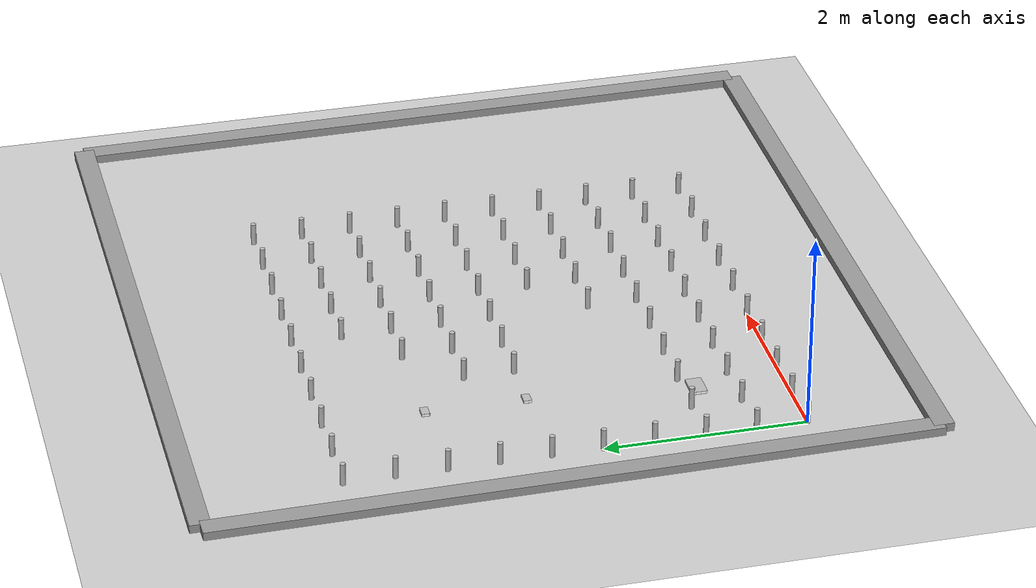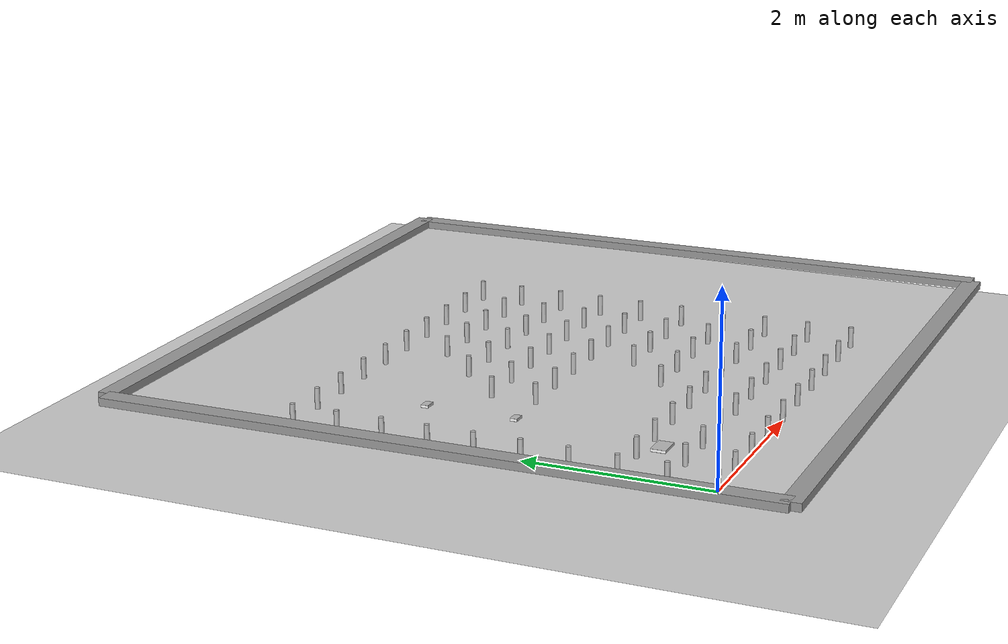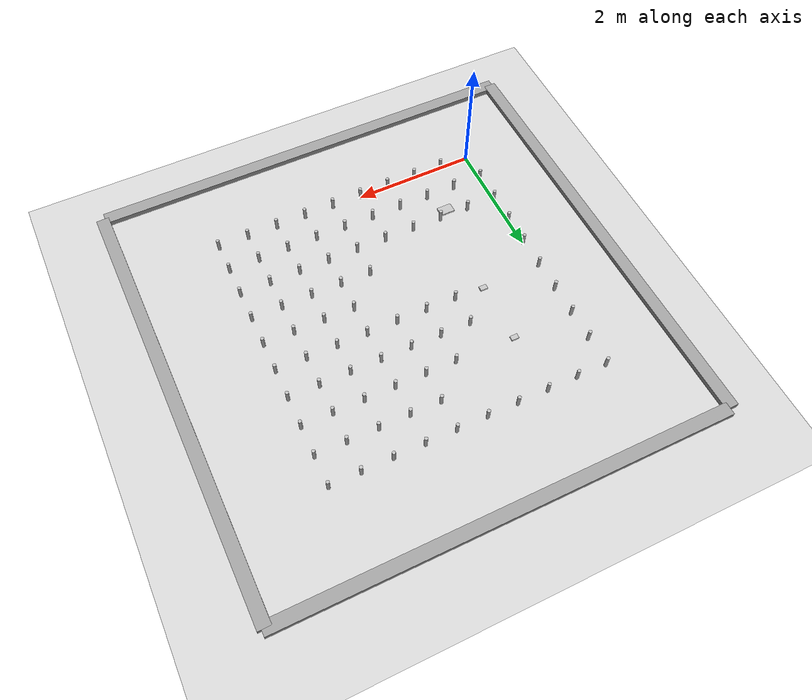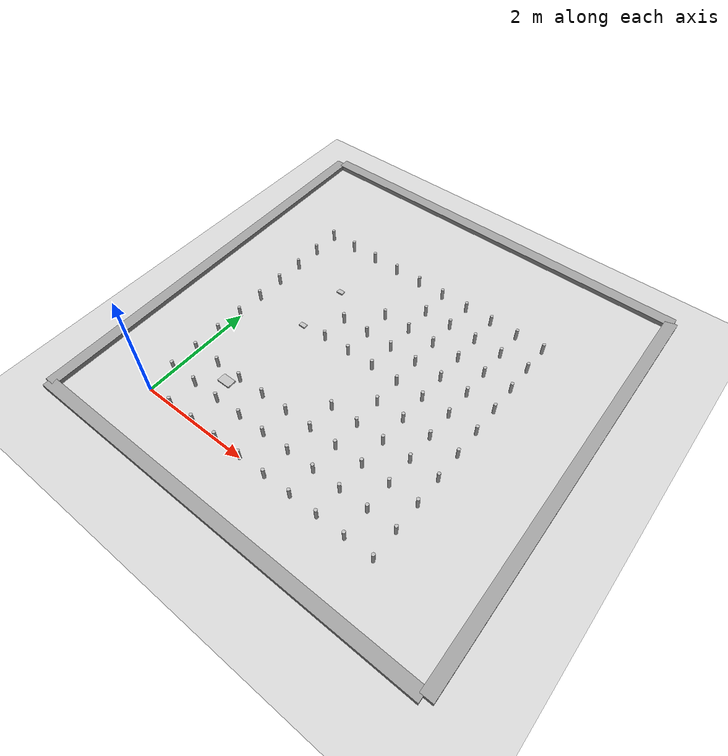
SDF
<sdf version="1.6">
 <world name="default">
  <light name="sun" type="directional">
   <pose>0 0 10 0 -0 0</pose>
   <diffuse>0.8 0.8 0.8 1</diffuse>
   <specular>0.1 0.1 0.1 1</specular>
   <attenuation>
    <range>1000</range>
    <constant>0.9</constant>
    <linear>0.01</linear>
    <quadratic>0.001</quadratic>
   </attenuation>
   <direction>-0.5 0.5 -1</direction>
  </light>
  <model name="ground_plane">
   <static>1</static>
   <link name="link">
    <collision name="collision">
     <geometry><plane><normal>0 0 1</normal><size>100 100</size></plane></geometry>
     <surface><friction><ode><mu>100</mu><mu2>50</mu2></ode></friction></surface>
    </collision>
    <visual name="visual">
     <cast_shadows>0</cast_shadows>
     <geometry><plane><normal>0 0 1</normal><size>100 100</size></plane></geometry>
     <material>
      <script><uri>file://media/materials/scripts/gazebo.material</uri><name>Gazebo/Grey</name></script>
     </material>
    </visual>
   </link>
  </model>
  <gravity>0 0 -9.8</gravity>
  <magnetic_field>6e-06 2.3e-05 -4.2e-05</magnetic_field>
  <atmosphere type="adiabatic"/>
  <physics name="default_physics" default="0" type="ode">
   <max_step_size>0.001</max_step_size>
   <real_time_factor>1</real_time_factor>
   <real_time_update_rate>1000</real_time_update_rate>
  </physics>
  <scene><ambient>0.4 0.4 0.4 1</ambient><background>0.7 0.7 0.7 1</background><shadows>1</shadows></scene>
  <spherical_coordinates>
   <surface_model>EARTH_WGS84</surface_model>
   <latitude_deg>0</latitude_deg>
   <longitude_deg>0</longitude_deg>
   <elevation>0</elevation>
   <heading_deg>0</heading_deg>
  </spherical_coordinates>
  <model name="wall1">
   <static>1</static>
   <link name="link">
    <pose>0 0 0.42 0 -0 0</pose>
    <collision name="collision"><geometry><box><size>7 0.2 0.084</size></box></geometry></collision>
    <visual name="visual">
     <cast_shadows>0</cast_shadows>
     <geometry><box><size>7 0.2 0.084</size></box></geometry>
     <material>
      <script>
       <uri>model://grey_wall/materials/scripts</uri>
       <uri>model://grey_wall/materials/textures</uri>
       <name>vrc/grey_wall</name>
      </script>
     </material>
    </visual>
   </link>
   <pose>-1 2.5 0 0 -0 -1.55905</pose>
  </model>
  <model name="wall2">
   <static>1</static>
   <link name="link">
    <pose>0 0 0.42 0 -0 0</pose>
    <collision name="collision"><geometry><box><size>7 0.2 0.084</size></box></geometry></collision>
    <visual name="visual">
     <cast_shadows>0</cast_shadows>
     <geometry><box><size>7 0.2 0.084</size></box></geometry>
     <material>
      <script>
       <uri>model://grey_wall/materials/scripts</uri>
       <uri>model://grey_wall/materials/textures</uri>
       <name>vrc/grey_wall</name>
      </script>
     </material>
    </visual>
   </link>
   <pose>2.5 6.0 0 0 -0 0</pose>
  </model>
  <model name="wall3">
   <static>1</static>
   <link name="link">
    <pose>0 0 0.42 0 -0 0</pose>
    <collision name="collision"><geometry><box><size>7 0.2 0.084</size></box></geometry></collision>
    <visual name="visual">
     <cast_shadows>0</cast_shadows>
     <geometry><box><size>7 0.2 0.084</size></box></geometry>
     <material>
      <script>
       <uri>model://grey_wall/materials/scripts</uri>
       <uri>model://grey_wall/materials/textures</uri>
       <name>vrc/grey_wall</name>
      </script>
     </material>
    </visual>
   </link>
   <pose>6.0 2.5 0 0 -0 -1.55905</pose>
  </model>
  <model name="wall4">
   <static>1</static>
   <link name="link">
    <pose>0 0 0.42 0 -0 0</pose>
    <collision name="collision"><geometry><box><size>7 0.2 0.084</size></box></geometry></collision>
    <visual name="visual">
     <cast_shadows>0</cast_shadows>
     <geometry><box><size>7 0.2 0.084</size></box></geometry>
     <material>
      <script>
       <uri>model://grey_wall/materials/scripts</uri>
       <uri>model://grey_wall/materials/textures</uri>
       <name>vrc/grey_wall</name>
      </script>
     </material>
    </visual>
   </link>
   <pose>2.5 -1 0 0 -0 0</pose>
  </model>
  <model name="can0.00.0">
   <link name="link">
    <pose>0 0 0.115 0 -0 0</pose>
    <inertial>
     <mass>39</mass>
     <inertia><ixx>0.00058</ixx><ixy>0</ixy><ixz>0</ixz><iyy>0.00058</iyy><iyz>0</iyz><izz>0.00019</izz></inertia>
    </inertial>
    <collision name="collision">
     <geometry><cylinder><radius>0.0275</radius><length>0.23</length></cylinder></geometry>
    </collision>
    <visual name="visual">
     <geometry><cylinder><radius>0.0275</radius><length>0.23</length></cylinder></geometry>
     <material>
      <script>
       <uri>model://beer/materials/scripts</uri>
       <uri>model://beer/materials/textures</uri>
       <name>Beer/Diffuse</name>
      </script>
     </material>
    </visual>
   </link>
   <pose>0.0 0.0 -2e-06 1e-06 0 -9.5e-05</pose>
  </model>
  <model name="can0.00.5">
   <link name="link">
    <pose>0 0 0.115 0 -0 0</pose>
    <inertial>
     <mass>39</mass>
     <inertia><ixx>0.00058</ixx><ixy>0</ixy><ixz>0</ixz><iyy>0.00058</iyy><iyz>0</iyz><izz>0.00019</izz></inertia>
    </inertial>
    <collision name="collision">
     <geometry><cylinder><radius>0.0275</radius><length>0.23</length></cylinder></geometry>
    </collision>
    <visual name="visual">
     <geometry><cylinder><radius>0.0275</radius><length>0.23</length></cylinder></geometry>
     <material>
      <script>
       <uri>model://beer/materials/scripts</uri>
       <uri>model://beer/materials/textures</uri>
       <name>Beer/Diffuse</name>
      </script>
     </material>
    </visual>
   </link>
   <pose>0.0 0.5 -2e-06 1e-06 0 -9.5e-05</pose>
  </model>
  <model name="can0.01.0">
   <link name="link">
    <pose>0 0 0.115 0 -0 0</pose>
    <inertial>
     <mass>39</mass>
     <inertia><ixx>0.00058</ixx><ixy>0</ixy><ixz>0</ixz><iyy>0.00058</iyy><iyz>0</iyz><izz>0.00019</izz></inertia>
    </inertial>
    <collision name="collision">
     <geometry><cylinder><radius>0.0275</radius><length>0.23</length></cylinder></geometry>
    </collision>
    <visual name="visual">
     <geometry><cylinder><radius>0.0275</radius><length>0.23</length></cylinder></geometry>
     <material>
      <script>
       <uri>model://beer/materials/scripts</uri>
       <uri>model://beer/materials/textures</uri>
       <name>Beer/Diffuse</name>
      </script>
     </material>
    </visual>
   </link>
   <pose>0.0 1.0 -2e-06 1e-06 0 -9.5e-05</pose>
  </model>
  <model name="can0.01.5">
   <link name="link">
    <pose>0 0 0.115 0 -0 0</pose>
    <inertial>
     <mass>39</mass>
     <inertia><ixx>0.00058</ixx><ixy>0</ixy><ixz>0</ixz><iyy>0.00058</iyy><iyz>0</iyz><izz>0.00019</izz></inertia>
    </inertial>
    <collision name="collision">
     <geometry><cylinder><radius>0.0275</radius><length>0.23</length></cylinder></geometry>
    </collision>
    <visual name="visual">
     <geometry><cylinder><radius>0.0275</radius><length>0.23</length></cylinder></geometry>
     <material>
      <script>
       <uri>model://beer/materials/scripts</uri>
       <uri>model://beer/materials/textures</uri>
       <name>Beer/Diffuse</name>
      </script>
     </material>
    </visual>
   </link>
   <pose>0.0 1.5 -2e-06 1e-06 0 -9.5e-05</pose>
  </model>
  <model name="can0.02.0">
   <link name="link">
    <pose>0 0 0.115 0 -0 0</pose>
    <inertial>
     <mass>39</mass>
     <inertia><ixx>0.00058</ixx><ixy>0</ixy><ixz>0</ixz><iyy>0.00058</iyy><iyz>0</iyz><izz>0.00019</izz></inertia>
    </inertial>
    <collision name="collision">
     <geometry><cylinder><radius>0.0275</radius><length>0.23</length></cylinder></geometry>
    </collision>
    <visual name="visual">
     <geometry><cylinder><radius>0.0275</radius><length>0.23</length></cylinder></geometry>
     <material>
      <script>
       <uri>model://beer/materials/scripts</uri>
       <uri>model://beer/materials/textures</uri>
       <name>Beer/Diffuse</name>
      </script>
     </material>
    </visual>
   </link>
   <pose>0.0 2.0 -2e-06 1e-06 0 -9.5e-05</pose>
  </model>
  <model name="can0.02.5">
   <link name="link">
    <pose>0 0 0.115 0 -0 0</pose>
    <inertial>
     <mass>39</mass>
     <inertia><ixx>0.00058</ixx><ixy>0</ixy><ixz>0</ixz><iyy>0.00058</iyy><iyz>0</iyz><izz>0.00019</izz></inertia>
    </inertial>
    <collision name="collision">
     <geometry><cylinder><radius>0.0275</radius><length>0.23</length></cylinder></geometry>
    </collision>
    <visual name="visual">
     <geometry><cylinder><radius>0.0275</radius><length>0.23</length></cylinder></geometry>
     <material>
      <script>
       <uri>model://beer/materials/scripts</uri>
       <uri>model://beer/materials/textures</uri>
       <name>Beer/Diffuse</name>
      </script>
     </material>
    </visual>
   </link>
   <pose>0.0 2.5 -2e-06 1e-06 0 -9.5e-05</pose>
  </model>
  <model name="can0.03.0">
   <link name="link">
    <pose>0 0 0.115 0 -0 0</pose>
    <inertial>
     <mass>39</mass>
     <inertia><ixx>0.00058</ixx><ixy>0</ixy><ixz>0</ixz><iyy>0.00058</iyy><iyz>0</iyz><izz>0.00019</izz></inertia>
    </inertial>
    <collision name="collision">
     <geometry><cylinder><radius>0.0275</radius><length>0.23</length></cylinder></geometry>
    </collision>
    <visual name="visual">
     <geometry><cylinder><radius>0.0275</radius><length>0.23</length></cylinder></geometry>
     <material>
      <script>
       <uri>model://beer/materials/scripts</uri>
       <uri>model://beer/materials/textures</uri>
       <name>Beer/Diffuse</name>
      </script>
     </material>
    </visual>
   </link>
   <pose>0.0 3.0 -2e-06 1e-06 0 -9.5e-05</pose>
  </model>
  <model name="can0.03.5">
   <link name="link">
    <pose>0 0 0.115 0 -0 0</pose>
    <inertial>
     <mass>39</mass>
     <inertia><ixx>0.00058</ixx><ixy>0</ixy><ixz>0</ixz><iyy>0.00058</iyy><iyz>0</iyz><izz>0.00019</izz></inertia>
    </inertial>
    <collision name="collision">
     <geometry><cylinder><radius>0.0275</radius><length>0.23</length></cylinder></geometry>
    </collision>
    <visual name="visual">
     <geometry><cylinder><radius>0.0275</radius><length>0.23</length></cylinder></geometry>
     <material>
      <script>
       <uri>model://beer/materials/scripts</uri>
       <uri>model://beer/materials/textures</uri>
       <name>Beer/Diffuse</name>
      </script>
     </material>
    </visual>
   </link>
   <pose>0.0 3.5 -2e-06 1e-06 0 -9.5e-05</pose>
  </model>
  <model name="can0.04.0">
   <link name="link">
    <pose>0 0 0.115 0 -0 0</pose>
    <inertial>
     <mass>39</mass>
     <inertia><ixx>0.00058</ixx><ixy>0</ixy><ixz>0</ixz><iyy>0.00058</iyy><iyz>0</iyz><izz>0.00019</izz></inertia>
    </inertial>
    <collision name="collision">
     <geometry><cylinder><radius>0.0275</radius><length>0.23</length></cylinder></geometry>
    </collision>
    <visual name="visual">
     <geometry><cylinder><radius>0.0275</radius><length>0.23</length></cylinder></geometry>
     <material>
      <script>
       <uri>model://beer/materials/scripts</uri>
       <uri>model://beer/materials/textures</uri>
       <name>Beer/Diffuse</name>
      </script>
     </material>
    </visual>
   </link>
   <pose>0.0 4.0 -2e-06 1e-06 0 -9.5e-05</pose>
  </model>
  <model name="can0.04.5">
   <link name="link">
    <pose>0 0 0.115 0 -0 0</pose>
    <inertial>
     <mass>39</mass>
     <inertia><ixx>0.00058</ixx><ixy>0</ixy><ixz>0</ixz><iyy>0.00058</iyy><iyz>0</iyz><izz>0.00019</izz></inertia>
    </inertial>
    <collision name="collision">
     <geometry><cylinder><radius>0.0275</radius><length>0.23</length></cylinder></geometry>
    </collision>
    <visual name="visual">
     <geometry><cylinder><radius>0.0275</radius><length>0.23</length></cylinder></geometry>
     <material>
      <script>
       <uri>model://beer/materials/scripts</uri>
       <uri>model://beer/materials/textures</uri>
       <name>Beer/Diffuse</name>
      </script>
     </material>
    </visual>
   </link>
   <pose>0.0 4.5 -2e-06 1e-06 0 -9.5e-05</pose>
  </model>
  <model name="can0.50.0">
   <link name="link">
    <pose>0 0 0.115 0 -0 0</pose>
    <inertial>
     <mass>39</mass>
     <inertia><ixx>0.00058</ixx><ixy>0</ixy><ixz>0</ixz><iyy>0.00058</iyy><iyz>0</iyz><izz>0.00019</izz></inertia>
    </inertial>
    <collision name="collision">
     <geometry><cylinder><radius>0.0275</radius><length>0.23</length></cylinder></geometry>
    </collision>
    <visual name="visual">
     <geometry><cylinder><radius>0.0275</radius><length>0.23</length></cylinder></geometry>
     <material>
      <script>
       <uri>model://beer/materials/scripts</uri>
       <uri>model://beer/materials/textures</uri>
       <name>Beer/Diffuse</name>
      </script>
     </material>
    </visual>
   </link>
   <pose>0.5 0.0 -2e-06 1e-06 0 -9.5e-05</pose>
  </model>
  <model name="can0.50.5">
   <link name="link">
    <pose>0 0 0.115 0 -0 0</pose>
    <inertial>
     <mass>39</mass>
     <inertia><ixx>0.00058</ixx><ixy>0</ixy><ixz>0</ixz><iyy>0.00058</iyy><iyz>0</iyz><izz>0.00019</izz></inertia>
    </inertial>
    <collision name="collision">
     <geometry><cylinder><radius>0.0275</radius><length>0.23</length></cylinder></geometry>
    </collision>
    <visual name="visual">
     <geometry><cylinder><radius>0.0275</radius><length>0.23</length></cylinder></geometry>
     <material>
      <script>
       <uri>model://beer/materials/scripts</uri>
       <uri>model://beer/materials/textures</uri>
       <name>Beer/Diffuse</name>
      </script>
     </material>
    </visual>
   </link>
   <pose>0.5 0.5 -2e-06 1e-06 0 -9.5e-05</pose>
  </model>
  <model name="can0.51.0">
   <link name="link">
    <pose>0 0 0.115 0 -0 0</pose>
    <inertial>
     <mass>39</mass>
     <inertia><ixx>0.00058</ixx><ixy>0</ixy><ixz>0</ixz><iyy>0.00058</iyy><iyz>0</iyz><izz>0.00019</izz></inertia>
    </inertial>
    <collision name="collision">
     <geometry><cylinder><radius>0.0275</radius><length>0.23</length></cylinder></geometry>
    </collision>
    <visual name="visual">
     <geometry><cylinder><radius>0.0275</radius><length>0.23</length></cylinder></geometry>
     <material>
      <script>
       <uri>model://beer/materials/scripts</uri>
       <uri>model://beer/materials/textures</uri>
       <name>Beer/Diffuse</name>
      </script>
     </material>
    </visual>
   </link>
   <pose>0.5 1.0 -2e-06 1e-06 0 -9.5e-05</pose>
  </model>
  <model name="can0.54.5">
   <link name="link">
    <pose>0 0 0.115 0 -0 0</pose>
    <inertial>
     <mass>39</mass>
     <inertia><ixx>0.00058</ixx><ixy>0</ixy><ixz>0</ixz><iyy>0.00058</iyy><iyz>0</iyz><izz>0.00019</izz></inertia>
    </inertial>
    <collision name="collision">
     <geometry><cylinder><radius>0.0275</radius><length>0.23</length></cylinder></geometry>
    </collision>
    <visual name="visual">
     <geometry><cylinder><radius>0.0275</radius><length>0.23</length></cylinder></geometry>
     <material>
      <script>
       <uri>model://beer/materials/scripts</uri>
       <uri>model://beer/materials/textures</uri>
       <name>Beer/Diffuse</name>
      </script>
     </material>
    </visual>
   </link>
   <pose>0.5 4.5 -2e-06 1e-06 0 -9.5e-05</pose>
  </model>
  <model name="can1.00.0">
   <link name="link">
    <pose>0 0 0.115 0 -0 0</pose>
    <inertial>
     <mass>39</mass>
     <inertia><ixx>0.00058</ixx><ixy>0</ixy><ixz>0</ixz><iyy>0.00058</iyy><iyz>0</iyz><izz>0.00019</izz></inertia>
    </inertial>
    <collision name="collision">
     <geometry><cylinder><radius>0.0275</radius><length>0.23</length></cylinder></geometry>
    </collision>
    <visual name="visual">
     <geometry><cylinder><radius>0.0275</radius><length>0.23</length></cylinder></geometry>
     <material>
      <script>
       <uri>model://beer/materials/scripts</uri>
       <uri>model://beer/materials/textures</uri>
       <name>Beer/Diffuse</name>
      </script>
     </material>
    </visual>
   </link>
   <pose>1.0 0.0 -2e-06 1e-06 0 -9.5e-05</pose>
  </model>
  <model name="can1.00.5">
   <link name="link">
    <pose>0 0 0.115 0 -0 0</pose>
    <inertial>
     <mass>39</mass>
     <inertia><ixx>0.00058</ixx><ixy>0</ixy><ixz>0</ixz><iyy>0.00058</iyy><iyz>0</iyz><izz>0.00019</izz></inertia>
    </inertial>
    <collision name="collision">
     <geometry><cylinder><radius>0.0275</radius><length>0.23</length></cylinder></geometry>
    </collision>
    <visual name="visual">
     <geometry><cylinder><radius>0.0275</radius><length>0.23</length></cylinder></geometry>
     <material>
      <script>
       <uri>model://beer/materials/scripts</uri>
       <uri>model://beer/materials/textures</uri>
       <name>Beer/Diffuse</name>
      </script>
     </material>
    </visual>
   </link>
   <pose>1.0 0.5 -2e-06 1e-06 0 -9.5e-05</pose>
  </model>
  <model name="can1.01.0">
   <link name="link">
    <pose>0 0 0.115 0 -0 0</pose>
    <inertial>
     <mass>39</mass>
     <inertia><ixx>0.00058</ixx><ixy>0</ixy><ixz>0</ixz><iyy>0.00058</iyy><iyz>0</iyz><izz>0.00019</izz></inertia>
    </inertial>
    <collision name="collision">
     <geometry><cylinder><radius>0.0275</radius><length>0.23</length></cylinder></geometry>
    </collision>
    <visual name="visual">
     <geometry><cylinder><radius>0.0275</radius><length>0.23</length></cylinder></geometry>
     <material>
      <script>
       <uri>model://beer/materials/scripts</uri>
       <uri>model://beer/materials/textures</uri>
       <name>Beer/Diffuse</name>
      </script>
     </material>
    </visual>
   </link>
   <pose>1.0 1.0 -2e-06 1e-06 0 -9.5e-05</pose>
  </model>
  <model name="can1.04.5">
   <link name="link">
    <pose>0 0 0.115 0 -0 0</pose>
    <inertial>
     <mass>39</mass>
     <inertia><ixx>0.00058</ixx><ixy>0</ixy><ixz>0</ixz><iyy>0.00058</iyy><iyz>0</iyz><izz>0.00019</izz></inertia>
    </inertial>
    <collision name="collision">
     <geometry><cylinder><radius>0.0275</radius><length>0.23</length></cylinder></geometry>
    </collision>
    <visual name="visual">
     <geometry><cylinder><radius>0.0275</radius><length>0.23</length></cylinder></geometry>
     <material>
      <script>
       <uri>model://beer/materials/scripts</uri>
       <uri>model://beer/materials/textures</uri>
       <name>Beer/Diffuse</name>
      </script>
     </material>
    </visual>
   </link>
   <pose>1.0 4.5 -2e-06 1e-06 0 -9.5e-05</pose>
  </model>
  <model name="can1.50.0">
   <link name="link">
    <pose>0 0 0.115 0 -0 0</pose>
    <inertial>
     <mass>39</mass>
     <inertia><ixx>0.00058</ixx><ixy>0</ixy><ixz>0</ixz><iyy>0.00058</iyy><iyz>0</iyz><izz>0.00019</izz></inertia>
    </inertial>
    <collision name="collision">
     <geometry><cylinder><radius>0.0275</radius><length>0.23</length></cylinder></geometry>
    </collision>
    <visual name="visual">
     <geometry><cylinder><radius>0.0275</radius><length>0.23</length></cylinder></geometry>
     <material>
      <script>
       <uri>model://beer/materials/scripts</uri>
       <uri>model://beer/materials/textures</uri>
       <name>Beer/Diffuse</name>
      </script>
     </material>
    </visual>
   </link>
   <pose>1.5 0.0 -2e-06 1e-06 0 -9.5e-05</pose>
  </model>
  <model name="can1.50.5">
   <link name="link">
    <pose>0 0 0.115 0 -0 0</pose>
    <inertial>
     <mass>39</mass>
     <inertia><ixx>0.00058</ixx><ixy>0</ixy><ixz>0</ixz><iyy>0.00058</iyy><iyz>0</iyz><izz>0.00019</izz></inertia>
    </inertial>
    <collision name="collision">
     <geometry><cylinder><radius>0.0275</radius><length>0.23</length></cylinder></geometry>
    </collision>
    <visual name="visual">
     <geometry><cylinder><radius>0.0275</radius><length>0.23</length></cylinder></geometry>
     <material>
      <script>
       <uri>model://beer/materials/scripts</uri>
       <uri>model://beer/materials/textures</uri>
       <name>Beer/Diffuse</name>
      </script>
     </material>
    </visual>
   </link>
   <pose>1.5 0.5 -2e-06 1e-06 0 -9.5e-05</pose>
  </model>
  <model name="can1.51.0">
   <link name="link">
    <pose>0 0 0.115 0 -0 0</pose>
    <inertial>
     <mass>39</mass>
     <inertia><ixx>0.00058</ixx><ixy>0</ixy><ixz>0</ixz><iyy>0.00058</iyy><iyz>0</iyz><izz>0.00019</izz></inertia>
    </inertial>
    <collision name="collision">
     <geometry><cylinder><radius>0.0275</radius><length>0.23</length></cylinder></geometry>
    </collision>
    <visual name="visual">
     <geometry><cylinder><radius>0.0275</radius><length>0.23</length></cylinder></geometry>
     <material>
      <script>
       <uri>model://beer/materials/scripts</uri>
       <uri>model://beer/materials/textures</uri>
       <name>Beer/Diffuse</name>
      </script>
     </material>
    </visual>
   </link>
   <pose>1.5 1.0 -2e-06 1e-06 0 -9.5e-05</pose>
  </model>
  <model name="can1.52.5">
   <link name="link">
    <pose>0 0 0.115 0 -0 0</pose>
    <inertial>
     <mass>39</mass>
     <inertia><ixx>0.00058</ixx><ixy>0</ixy><ixz>0</ixz><iyy>0.00058</iyy><iyz>0</iyz><izz>0.00019</izz></inertia>
    </inertial>
    <collision name="collision">
     <geometry><cylinder><radius>0.0275</radius><length>0.23</length></cylinder></geometry>
    </collision>
    <visual name="visual">
     <geometry><cylinder><radius>0.0275</radius><length>0.23</length></cylinder></geometry>
     <material>
      <script>
       <uri>model://beer/materials/scripts</uri>
       <uri>model://beer/materials/textures</uri>
       <name>Beer/Diffuse</name>
      </script>
     </material>
    </visual>
   </link>
   <pose>1.5 2.5 -2e-06 1e-06 0 -9.5e-05</pose>
  </model>
  <model name="can1.53.0">
   <link name="link">
    <pose>0 0 0.115 0 -0 0</pose>
    <inertial>
     <mass>39</mass>
     <inertia><ixx>0.00058</ixx><ixy>0</ixy><ixz>0</ixz><iyy>0.00058</iyy><iyz>0</iyz><izz>0.00019</izz></inertia>
    </inertial>
    <collision name="collision">
     <geometry><cylinder><radius>0.0275</radius><length>0.23</length></cylinder></geometry>
    </collision>
    <visual name="visual">
     <geometry><cylinder><radius>0.0275</radius><length>0.23</length></cylinder></geometry>
     <material>
      <script>
       <uri>model://beer/materials/scripts</uri>
       <uri>model://beer/materials/textures</uri>
       <name>Beer/Diffuse</name>
      </script>
     </material>
    </visual>
   </link>
   <pose>1.5 3.0 -2e-06 1e-06 0 -9.5e-05</pose>
  </model>
  <model name="can1.54.5">
   <link name="link">
    <pose>0 0 0.115 0 -0 0</pose>
    <inertial>
     <mass>39</mass>
     <inertia><ixx>0.00058</ixx><ixy>0</ixy><ixz>0</ixz><iyy>0.00058</iyy><iyz>0</iyz><izz>0.00019</izz></inertia>
    </inertial>
    <collision name="collision">
     <geometry><cylinder><radius>0.0275</radius><length>0.23</length></cylinder></geometry>
    </collision>
    <visual name="visual">
     <geometry><cylinder><radius>0.0275</radius><length>0.23</length></cylinder></geometry>
     <material>
      <script>
       <uri>model://beer/materials/scripts</uri>
       <uri>model://beer/materials/textures</uri>
       <name>Beer/Diffuse</name>
      </script>
     </material>
    </visual>
   </link>
   <pose>1.5 4.5 -2e-06 1e-06 0 -9.5e-05</pose>
  </model>
  <model name="can2.00.0">
   <link name="link">
    <pose>0 0 0.115 0 -0 0</pose>
    <inertial>
     <mass>39</mass>
     <inertia><ixx>0.00058</ixx><ixy>0</ixy><ixz>0</ixz><iyy>0.00058</iyy><iyz>0</iyz><izz>0.00019</izz></inertia>
    </inertial>
    <collision name="collision">
     <geometry><cylinder><radius>0.0275</radius><length>0.23</length></cylinder></geometry>
    </collision>
    <visual name="visual">
     <geometry><cylinder><radius>0.0275</radius><length>0.23</length></cylinder></geometry>
     <material>
      <script>
       <uri>model://beer/materials/scripts</uri>
       <uri>model://beer/materials/textures</uri>
       <name>Beer/Diffuse</name>
      </script>
     </material>
    </visual>
   </link>
   <pose>2.0 0.0 -2e-06 1e-06 0 -9.5e-05</pose>
  </model>
  <model name="can2.00.5">
   <link name="link">
    <pose>0 0 0.115 0 -0 0</pose>
    <inertial>
     <mass>39</mass>
     <inertia><ixx>0.00058</ixx><ixy>0</ixy><ixz>0</ixz><iyy>0.00058</iyy><iyz>0</iyz><izz>0.00019</izz></inertia>
    </inertial>
    <collision name="collision">
     <geometry><cylinder><radius>0.0275</radius><length>0.23</length></cylinder></geometry>
    </collision>
    <visual name="visual">
     <geometry><cylinder><radius>0.0275</radius><length>0.23</length></cylinder></geometry>
     <material>
      <script>
       <uri>model://beer/materials/scripts</uri>
       <uri>model://beer/materials/textures</uri>
       <name>Beer/Diffuse</name>
      </script>
     </material>
    </visual>
   </link>
   <pose>2.0 0.5 -2e-06 1e-06 0 -9.5e-05</pose>
  </model>
  <model name="can2.01.0">
   <link name="link">
    <pose>0 0 0.115 0 -0 0</pose>
    <inertial>
     <mass>39</mass>
     <inertia><ixx>0.00058</ixx><ixy>0</ixy><ixz>0</ixz><iyy>0.00058</iyy><iyz>0</iyz><izz>0.00019</izz></inertia>
    </inertial>
    <collision name="collision">
     <geometry><cylinder><radius>0.0275</radius><length>0.23</length></cylinder></geometry>
    </collision>
    <visual name="visual">
     <geometry><cylinder><radius>0.0275</radius><length>0.23</length></cylinder></geometry>
     <material>
      <script>
       <uri>model://beer/materials/scripts</uri>
       <uri>model://beer/materials/textures</uri>
       <name>Beer/Diffuse</name>
      </script>
     </material>
    </visual>
   </link>
   <pose>2.0 1.0 -2e-06 1e-06 0 -9.5e-05</pose>
  </model>
  <model name="can2.02.5">
   <link name="link">
    <pose>0 0 0.115 0 -0 0</pose>
    <inertial>
     <mass>39</mass>
     <inertia><ixx>0.00058</ixx><ixy>0</ixy><ixz>0</ixz><iyy>0.00058</iyy><iyz>0</iyz><izz>0.00019</izz></inertia>
    </inertial>
    <collision name="collision">
     <geometry><cylinder><radius>0.0275</radius><length>0.23</length></cylinder></geometry>
    </collision>
    <visual name="visual">
     <geometry><cylinder><radius>0.0275</radius><length>0.23</length></cylinder></geometry>
     <material>
      <script>
       <uri>model://beer/materials/scripts</uri>
       <uri>model://beer/materials/textures</uri>
       <name>Beer/Diffuse</name>
      </script>
     </material>
    </visual>
   </link>
   <pose>2.0 2.5 -2e-06 1e-06 0 -9.5e-05</pose>
  </model>
  <model name="can2.03.0">
   <link name="link">
    <pose>0 0 0.115 0 -0 0</pose>
    <inertial>
     <mass>39</mass>
     <inertia><ixx>0.00058</ixx><ixy>0</ixy><ixz>0</ixz><iyy>0.00058</iyy><iyz>0</iyz><izz>0.00019</izz></inertia>
    </inertial>
    <collision name="collision">
     <geometry><cylinder><radius>0.0275</radius><length>0.23</length></cylinder></geometry>
    </collision>
    <visual name="visual">
     <geometry><cylinder><radius>0.0275</radius><length>0.23</length></cylinder></geometry>
     <material>
      <script>
       <uri>model://beer/materials/scripts</uri>
       <uri>model://beer/materials/textures</uri>
       <name>Beer/Diffuse</name>
      </script>
     </material>
    </visual>
   </link>
   <pose>2.0 3.0 -2e-06 1e-06 0 -9.5e-05</pose>
  </model>
  <model name="can2.03.5">
   <link name="link">
    <pose>0 0 0.115 0 -0 0</pose>
    <inertial>
     <mass>39</mass>
     <inertia><ixx>0.00058</ixx><ixy>0</ixy><ixz>0</ixz><iyy>0.00058</iyy><iyz>0</iyz><izz>0.00019</izz></inertia>
    </inertial>
    <collision name="collision">
     <geometry><cylinder><radius>0.0275</radius><length>0.23</length></cylinder></geometry>
    </collision>
    <visual name="visual">
     <geometry><cylinder><radius>0.0275</radius><length>0.23</length></cylinder></geometry>
     <material>
      <script>
       <uri>model://beer/materials/scripts</uri>
       <uri>model://beer/materials/textures</uri>
       <name>Beer/Diffuse</name>
      </script>
     </material>
    </visual>
   </link>
   <pose>2.0 3.5 -2e-06 1e-06 0 -9.5e-05</pose>
  </model>
  <model name="can2.04.5">
   <link name="link">
    <pose>0 0 0.115 0 -0 0</pose>
    <inertial>
     <mass>39</mass>
     <inertia><ixx>0.00058</ixx><ixy>0</ixy><ixz>0</ixz><iyy>0.00058</iyy><iyz>0</iyz><izz>0.00019</izz></inertia>
    </inertial>
    <collision name="collision">
     <geometry><cylinder><radius>0.0275</radius><length>0.23</length></cylinder></geometry>
    </collision>
    <visual name="visual">
     <geometry><cylinder><radius>0.0275</radius><length>0.23</length></cylinder></geometry>
     <material>
      <script>
       <uri>model://beer/materials/scripts</uri>
       <uri>model://beer/materials/textures</uri>
       <name>Beer/Diffuse</name>
      </script>
     </material>
    </visual>
   </link>
   <pose>2.0 4.5 -2e-06 1e-06 0 -9.5e-05</pose>
  </model>
  <model name="can2.50.0">
   <link name="link">
    <pose>0 0 0.115 0 -0 0</pose>
    <inertial>
     <mass>39</mass>
     <inertia><ixx>0.00058</ixx><ixy>0</ixy><ixz>0</ixz><iyy>0.00058</iyy><iyz>0</iyz><izz>0.00019</izz></inertia>
    </inertial>
    <collision name="collision">
     <geometry><cylinder><radius>0.0275</radius><length>0.23</length></cylinder></geometry>
    </collision>
    <visual name="visual">
     <geometry><cylinder><radius>0.0275</radius><length>0.23</length></cylinder></geometry>
     <material>
      <script>
       <uri>model://beer/materials/scripts</uri>
       <uri>model://beer/materials/textures</uri>
       <name>Beer/Diffuse</name>
      </script>
     </material>
    </visual>
   </link>
   <pose>2.5 0.0 -2e-06 1e-06 0 -9.5e-05</pose>
  </model>
  <model name="can2.50.5">
   <link name="link">
    <pose>0 0 0.115 0 -0 0</pose>
    <inertial>
     <mass>39</mass>
     <inertia><ixx>0.00058</ixx><ixy>0</ixy><ixz>0</ixz><iyy>0.00058</iyy><iyz>0</iyz><izz>0.00019</izz></inertia>
    </inertial>
    <collision name="collision">
     <geometry><cylinder><radius>0.0275</radius><length>0.23</length></cylinder></geometry>
    </collision>
    <visual name="visual">
     <geometry><cylinder><radius>0.0275</radius><length>0.23</length></cylinder></geometry>
     <material>
      <script>
       <uri>model://beer/materials/scripts</uri>
       <uri>model://beer/materials/textures</uri>
       <name>Beer/Diffuse</name>
      </script>
     </material>
    </visual>
   </link>
   <pose>2.5 0.5 -2e-06 1e-06 0 -9.5e-05</pose>
  </model>
  <model name="can2.51.0">
   <link name="link">
    <pose>0 0 0.115 0 -0 0</pose>
    <inertial>
     <mass>39</mass>
     <inertia><ixx>0.00058</ixx><ixy>0</ixy><ixz>0</ixz><iyy>0.00058</iyy><iyz>0</iyz><izz>0.00019</izz></inertia>
    </inertial>
    <collision name="collision">
     <geometry><cylinder><radius>0.0275</radius><length>0.23</length></cylinder></geometry>
    </collision>
    <visual name="visual">
     <geometry><cylinder><radius>0.0275</radius><length>0.23</length></cylinder></geometry>
     <material>
      <script>
       <uri>model://beer/materials/scripts</uri>
       <uri>model://beer/materials/textures</uri>
       <name>Beer/Diffuse</name>
      </script>
     </material>
    </visual>
   </link>
   <pose>2.5 1.0 -2e-06 1e-06 0 -9.5e-05</pose>
  </model>
  <model name="can2.51.5">
   <link name="link">
    <pose>0 0 0.115 0 -0 0</pose>
    <inertial>
     <mass>39</mass>
     <inertia><ixx>0.00058</ixx><ixy>0</ixy><ixz>0</ixz><iyy>0.00058</iyy><iyz>0</iyz><izz>0.00019</izz></inertia>
    </inertial>
    <collision name="collision">
     <geometry><cylinder><radius>0.0275</radius><length>0.23</length></cylinder></geometry>
    </collision>
    <visual name="visual">
     <geometry><cylinder><radius>0.0275</radius><length>0.23</length></cylinder></geometry>
     <material>
      <script>
       <uri>model://beer/materials/scripts</uri>
       <uri>model://beer/materials/textures</uri>
       <name>Beer/Diffuse</name>
      </script>
     </material>
    </visual>
   </link>
   <pose>2.5 1.5 -2e-06 1e-06 0 -9.5e-05</pose>
  </model>
  <model name="can2.52.5">
   <link name="link">
    <pose>0 0 0.115 0 -0 0</pose>
    <inertial>
     <mass>39</mass>
     <inertia><ixx>0.00058</ixx><ixy>0</ixy><ixz>0</ixz><iyy>0.00058</iyy><iyz>0</iyz><izz>0.00019</izz></inertia>
    </inertial>
    <collision name="collision">
     <geometry><cylinder><radius>0.0275</radius><length>0.23</length></cylinder></geometry>
    </collision>
    <visual name="visual">
     <geometry><cylinder><radius>0.0275</radius><length>0.23</length></cylinder></geometry>
     <material>
      <script>
       <uri>model://beer/materials/scripts</uri>
       <uri>model://beer/materials/textures</uri>
       <name>Beer/Diffuse</name>
      </script>
     </material>
    </visual>
   </link>
   <pose>2.5 2.5 -2e-06 1e-06 0 -9.5e-05</pose>
  </model>
  <model name="can2.53.0">
   <link name="link">
    <pose>0 0 0.115 0 -0 0</pose>
    <inertial>
     <mass>39</mass>
     <inertia><ixx>0.00058</ixx><ixy>0</ixy><ixz>0</ixz><iyy>0.00058</iyy><iyz>0</iyz><izz>0.00019</izz></inertia>
    </inertial>
    <collision name="collision">
     <geometry><cylinder><radius>0.0275</radius><length>0.23</length></cylinder></geometry>
    </collision>
    <visual name="visual">
     <geometry><cylinder><radius>0.0275</radius><length>0.23</length></cylinder></geometry>
     <material>
      <script>
       <uri>model://beer/materials/scripts</uri>
       <uri>model://beer/materials/textures</uri>
       <name>Beer/Diffuse</name>
      </script>
     </material>
    </visual>
   </link>
   <pose>2.5 3.0 -2e-06 1e-06 0 -9.5e-05</pose>
  </model>
  <model name="can2.53.5">
   <link name="link">
    <pose>0 0 0.115 0 -0 0</pose>
    <inertial>
     <mass>39</mass>
     <inertia><ixx>0.00058</ixx><ixy>0</ixy><ixz>0</ixz><iyy>0.00058</iyy><iyz>0</iyz><izz>0.00019</izz></inertia>
    </inertial>
    <collision name="collision">
     <geometry><cylinder><radius>0.0275</radius><length>0.23</length></cylinder></geometry>
    </collision>
    <visual name="visual">
     <geometry><cylinder><radius>0.0275</radius><length>0.23</length></cylinder></geometry>
     <material>
      <script>
       <uri>model://beer/materials/scripts</uri>
       <uri>model://beer/materials/textures</uri>
       <name>Beer/Diffuse</name>
      </script>
     </material>
    </visual>
   </link>
   <pose>2.5 3.5 -2e-06 1e-06 0 -9.5e-05</pose>
  </model>
  <model name="can2.54.0">
   <link name="link">
    <pose>0 0 0.115 0 -0 0</pose>
    <inertial>
     <mass>39</mass>
     <inertia><ixx>0.00058</ixx><ixy>0</ixy><ixz>0</ixz><iyy>0.00058</iyy><iyz>0</iyz><izz>0.00019</izz></inertia>
    </inertial>
    <collision name="collision">
     <geometry><cylinder><radius>0.0275</radius><length>0.23</length></cylinder></geometry>
    </collision>
    <visual name="visual">
     <geometry><cylinder><radius>0.0275</radius><length>0.23</length></cylinder></geometry>
     <material>
      <script>
       <uri>model://beer/materials/scripts</uri>
       <uri>model://beer/materials/textures</uri>
       <name>Beer/Diffuse</name>
      </script>
     </material>
    </visual>
   </link>
   <pose>2.5 4.0 -2e-06 1e-06 0 -9.5e-05</pose>
  </model>
  <model name="can2.54.5">
   <link name="link">
    <pose>0 0 0.115 0 -0 0</pose>
    <inertial>
     <mass>39</mass>
     <inertia><ixx>0.00058</ixx><ixy>0</ixy><ixz>0</ixz><iyy>0.00058</iyy><iyz>0</iyz><izz>0.00019</izz></inertia>
    </inertial>
    <collision name="collision">
     <geometry><cylinder><radius>0.0275</radius><length>0.23</length></cylinder></geometry>
    </collision>
    <visual name="visual">
     <geometry><cylinder><radius>0.0275</radius><length>0.23</length></cylinder></geometry>
     <material>
      <script>
       <uri>model://beer/materials/scripts</uri>
       <uri>model://beer/materials/textures</uri>
       <name>Beer/Diffuse</name>
      </script>
     </material>
    </visual>
   </link>
   <pose>2.5 4.5 -2e-06 1e-06 0 -9.5e-05</pose>
  </model>
  <model name="can3.00.0">
   <link name="link">
    <pose>0 0 0.115 0 -0 0</pose>
    <inertial>
     <mass>39</mass>
     <inertia><ixx>0.00058</ixx><ixy>0</ixy><ixz>0</ixz><iyy>0.00058</iyy><iyz>0</iyz><izz>0.00019</izz></inertia>
    </inertial>
    <collision name="collision">
     <geometry><cylinder><radius>0.0275</radius><length>0.23</length></cylinder></geometry>
    </collision>
    <visual name="visual">
     <geometry><cylinder><radius>0.0275</radius><length>0.23</length></cylinder></geometry>
     <material>
      <script>
       <uri>model://beer/materials/scripts</uri>
       <uri>model://beer/materials/textures</uri>
       <name>Beer/Diffuse</name>
      </script>
     </material>
    </visual>
   </link>
   <pose>3.0 0.0 -2e-06 1e-06 0 -9.5e-05</pose>
  </model>
  <model name="can3.00.5">
   <link name="link">
    <pose>0 0 0.115 0 -0 0</pose>
    <inertial>
     <mass>39</mass>
     <inertia><ixx>0.00058</ixx><ixy>0</ixy><ixz>0</ixz><iyy>0.00058</iyy><iyz>0</iyz><izz>0.00019</izz></inertia>
    </inertial>
    <collision name="collision">
     <geometry><cylinder><radius>0.0275</radius><length>0.23</length></cylinder></geometry>
    </collision>
    <visual name="visual">
     <geometry><cylinder><radius>0.0275</radius><length>0.23</length></cylinder></geometry>
     <material>
      <script>
       <uri>model://beer/materials/scripts</uri>
       <uri>model://beer/materials/textures</uri>
       <name>Beer/Diffuse</name>
      </script>
     </material>
    </visual>
   </link>
   <pose>3.0 0.5 -2e-06 1e-06 0 -9.5e-05</pose>
  </model>
  <model name="can3.01.0">
   <link name="link">
    <pose>0 0 0.115 0 -0 0</pose>
    <inertial>
     <mass>39</mass>
     <inertia><ixx>0.00058</ixx><ixy>0</ixy><ixz>0</ixz><iyy>0.00058</iyy><iyz>0</iyz><izz>0.00019</izz></inertia>
    </inertial>
    <collision name="collision">
     <geometry><cylinder><radius>0.0275</radius><length>0.23</length></cylinder></geometry>
    </collision>
    <visual name="visual">
     <geometry><cylinder><radius>0.0275</radius><length>0.23</length></cylinder></geometry>
     <material>
      <script>
       <uri>model://beer/materials/scripts</uri>
       <uri>model://beer/materials/textures</uri>
       <name>Beer/Diffuse</name>
      </script>
     </material>
    </visual>
   </link>
   <pose>3.0 1.0 -2e-06 1e-06 0 -9.5e-05</pose>
  </model>
  <model name="can3.01.5">
   <link name="link">
    <pose>0 0 0.115 0 -0 0</pose>
    <inertial>
     <mass>39</mass>
     <inertia><ixx>0.00058</ixx><ixy>0</ixy><ixz>0</ixz><iyy>0.00058</iyy><iyz>0</iyz><izz>0.00019</izz></inertia>
    </inertial>
    <collision name="collision">
     <geometry><cylinder><radius>0.0275</radius><length>0.23</length></cylinder></geometry>
    </collision>
    <visual name="visual">
     <geometry><cylinder><radius>0.0275</radius><length>0.23</length></cylinder></geometry>
     <material>
      <script>
       <uri>model://beer/materials/scripts</uri>
       <uri>model://beer/materials/textures</uri>
       <name>Beer/Diffuse</name>
      </script>
     </material>
    </visual>
   </link>
   <pose>3.0 1.5 -2e-06 1e-06 0 -9.5e-05</pose>
  </model>
  <model name="can3.02.0">
   <link name="link">
    <pose>0 0 0.115 0 -0 0</pose>
    <inertial>
     <mass>39</mass>
     <inertia><ixx>0.00058</ixx><ixy>0</ixy><ixz>0</ixz><iyy>0.00058</iyy><iyz>0</iyz><izz>0.00019</izz></inertia>
    </inertial>
    <collision name="collision">
     <geometry><cylinder><radius>0.0275</radius><length>0.23</length></cylinder></geometry>
    </collision>
    <visual name="visual">
     <geometry><cylinder><radius>0.0275</radius><length>0.23</length></cylinder></geometry>
     <material>
      <script>
       <uri>model://beer/materials/scripts</uri>
       <uri>model://beer/materials/textures</uri>
       <name>Beer/Diffuse</name>
      </script>
     </material>
    </visual>
   </link>
   <pose>3.0 2.0 -2e-06 1e-06 0 -9.5e-05</pose>
  </model>
  <model name="can3.02.5">
   <link name="link">
    <pose>0 0 0.115 0 -0 0</pose>
    <inertial>
     <mass>39</mass>
     <inertia><ixx>0.00058</ixx><ixy>0</ixy><ixz>0</ixz><iyy>0.00058</iyy><iyz>0</iyz><izz>0.00019</izz></inertia>
    </inertial>
    <collision name="collision">
     <geometry><cylinder><radius>0.0275</radius><length>0.23</length></cylinder></geometry>
    </collision>
    <visual name="visual">
     <geometry><cylinder><radius>0.0275</radius><length>0.23</length></cylinder></geometry>
     <material>
      <script>
       <uri>model://beer/materials/scripts</uri>
       <uri>model://beer/materials/textures</uri>
       <name>Beer/Diffuse</name>
      </script>
     </material>
    </visual>
   </link>
   <pose>3.0 2.5 -2e-06 1e-06 0 -9.5e-05</pose>
  </model>
  <model name="can3.03.0">
   <link name="link">
    <pose>0 0 0.115 0 -0 0</pose>
    <inertial>
     <mass>39</mass>
     <inertia><ixx>0.00058</ixx><ixy>0</ixy><ixz>0</ixz><iyy>0.00058</iyy><iyz>0</iyz><izz>0.00019</izz></inertia>
    </inertial>
    <collision name="collision">
     <geometry><cylinder><radius>0.0275</radius><length>0.23</length></cylinder></geometry>
    </collision>
    <visual name="visual">
     <geometry><cylinder><radius>0.0275</radius><length>0.23</length></cylinder></geometry>
     <material>
      <script>
       <uri>model://beer/materials/scripts</uri>
       <uri>model://beer/materials/textures</uri>
       <name>Beer/Diffuse</name>
      </script>
     </material>
    </visual>
   </link>
   <pose>3.0 3.0 -2e-06 1e-06 0 -9.5e-05</pose>
  </model>
  <model name="can3.03.5">
   <link name="link">
    <pose>0 0 0.115 0 -0 0</pose>
    <inertial>
     <mass>39</mass>
     <inertia><ixx>0.00058</ixx><ixy>0</ixy><ixz>0</ixz><iyy>0.00058</iyy><iyz>0</iyz><izz>0.00019</izz></inertia>
    </inertial>
    <collision name="collision">
     <geometry><cylinder><radius>0.0275</radius><length>0.23</length></cylinder></geometry>
    </collision>
    <visual name="visual">
     <geometry><cylinder><radius>0.0275</radius><length>0.23</length></cylinder></geometry>
     <material>
      <script>
       <uri>model://beer/materials/scripts</uri>
       <uri>model://beer/materials/textures</uri>
       <name>Beer/Diffuse</name>
      </script>
     </material>
    </visual>
   </link>
   <pose>3.0 3.5 -2e-06 1e-06 0 -9.5e-05</pose>
  </model>
  <model name="can3.04.0">
   <link name="link">
    <pose>0 0 0.115 0 -0 0</pose>
    <inertial>
     <mass>39</mass>
     <inertia><ixx>0.00058</ixx><ixy>0</ixy><ixz>0</ixz><iyy>0.00058</iyy><iyz>0</iyz><izz>0.00019</izz></inertia>
    </inertial>
    <collision name="collision">
     <geometry><cylinder><radius>0.0275</radius><length>0.23</length></cylinder></geometry>
    </collision>
    <visual name="visual">
     <geometry><cylinder><radius>0.0275</radius><length>0.23</length></cylinder></geometry>
     <material>
      <script>
       <uri>model://beer/materials/scripts</uri>
       <uri>model://beer/materials/textures</uri>
       <name>Beer/Diffuse</name>
      </script>
     </material>
    </visual>
   </link>
   <pose>3.0 4.0 -2e-06 1e-06 0 -9.5e-05</pose>
  </model>
  <model name="can3.04.5">
   <link name="link">
    <pose>0 0 0.115 0 -0 0</pose>
    <inertial>
     <mass>39</mass>
     <inertia><ixx>0.00058</ixx><ixy>0</ixy><ixz>0</ixz><iyy>0.00058</iyy><iyz>0</iyz><izz>0.00019</izz></inertia>
    </inertial>
    <collision name="collision">
     <geometry><cylinder><radius>0.0275</radius><length>0.23</length></cylinder></geometry>
    </collision>
    <visual name="visual">
     <geometry><cylinder><radius>0.0275</radius><length>0.23</length></cylinder></geometry>
     <material>
      <script>
       <uri>model://beer/materials/scripts</uri>
       <uri>model://beer/materials/textures</uri>
       <name>Beer/Diffuse</name>
      </script>
     </material>
    </visual>
   </link>
   <pose>3.0 4.5 -2e-06 1e-06 0 -9.5e-05</pose>
  </model>
  <model name="can3.50.0">
   <link name="link">
    <pose>0 0 0.115 0 -0 0</pose>
    <inertial>
     <mass>39</mass>
     <inertia><ixx>0.00058</ixx><ixy>0</ixy><ixz>0</ixz><iyy>0.00058</iyy><iyz>0</iyz><izz>0.00019</izz></inertia>
    </inertial>
    <collision name="collision">
     <geometry><cylinder><radius>0.0275</radius><length>0.23</length></cylinder></geometry>
    </collision>
    <visual name="visual">
     <geometry><cylinder><radius>0.0275</radius><length>0.23</length></cylinder></geometry>
     <material>
      <script>
       <uri>model://beer/materials/scripts</uri>
       <uri>model://beer/materials/textures</uri>
       <name>Beer/Diffuse</name>
      </script>
     </material>
    </visual>
   </link>
   <pose>3.5 0.0 -2e-06 1e-06 0 -9.5e-05</pose>
  </model>
  <model name="can3.50.5">
   <link name="link">
    <pose>0 0 0.115 0 -0 0</pose>
    <inertial>
     <mass>39</mass>
     <inertia><ixx>0.00058</ixx><ixy>0</ixy><ixz>0</ixz><iyy>0.00058</iyy><iyz>0</iyz><izz>0.00019</izz></inertia>
    </inertial>
    <collision name="collision">
     <geometry><cylinder><radius>0.0275</radius><length>0.23</length></cylinder></geometry>
    </collision>
    <visual name="visual">
     <geometry><cylinder><radius>0.0275</radius><length>0.23</length></cylinder></geometry>
     <material>
      <script>
       <uri>model://beer/materials/scripts</uri>
       <uri>model://beer/materials/textures</uri>
       <name>Beer/Diffuse</name>
      </script>
     </material>
    </visual>
   </link>
   <pose>3.5 0.5 -2e-06 1e-06 0 -9.5e-05</pose>
  </model>
  <model name="can3.51.0">
   <link name="link">
    <pose>0 0 0.115 0 -0 0</pose>
    <inertial>
     <mass>39</mass>
     <inertia><ixx>0.00058</ixx><ixy>0</ixy><ixz>0</ixz><iyy>0.00058</iyy><iyz>0</iyz><izz>0.00019</izz></inertia>
    </inertial>
    <collision name="collision">
     <geometry><cylinder><radius>0.0275</radius><length>0.23</length></cylinder></geometry>
    </collision>
    <visual name="visual">
     <geometry><cylinder><radius>0.0275</radius><length>0.23</length></cylinder></geometry>
     <material>
      <script>
       <uri>model://beer/materials/scripts</uri>
       <uri>model://beer/materials/textures</uri>
       <name>Beer/Diffuse</name>
      </script>
     </material>
    </visual>
   </link>
   <pose>3.5 1.0 -2e-06 1e-06 0 -9.5e-05</pose>
  </model>
  <model name="can3.51.5">
   <link name="link">
    <pose>0 0 0.115 0 -0 0</pose>
    <inertial>
     <mass>39</mass>
     <inertia><ixx>0.00058</ixx><ixy>0</ixy><ixz>0</ixz><iyy>0.00058</iyy><iyz>0</iyz><izz>0.00019</izz></inertia>
    </inertial>
    <collision name="collision">
     <geometry><cylinder><radius>0.0275</radius><length>0.23</length></cylinder></geometry>
    </collision>
    <visual name="visual">
     <geometry><cylinder><radius>0.0275</radius><length>0.23</length></cylinder></geometry>
     <material>
      <script>
       <uri>model://beer/materials/scripts</uri>
       <uri>model://beer/materials/textures</uri>
       <name>Beer/Diffuse</name>
      </script>
     </material>
    </visual>
   </link>
   <pose>3.5 1.5 -2e-06 1e-06 0 -9.5e-05</pose>
  </model>
  <model name="can3.52.0">
   <link name="link">
    <pose>0 0 0.115 0 -0 0</pose>
    <inertial>
     <mass>39</mass>
     <inertia><ixx>0.00058</ixx><ixy>0</ixy><ixz>0</ixz><iyy>0.00058</iyy><iyz>0</iyz><izz>0.00019</izz></inertia>
    </inertial>
    <collision name="collision">
     <geometry><cylinder><radius>0.0275</radius><length>0.23</length></cylinder></geometry>
    </collision>
    <visual name="visual">
     <geometry><cylinder><radius>0.0275</radius><length>0.23</length></cylinder></geometry>
     <material>
      <script>
       <uri>model://beer/materials/scripts</uri>
       <uri>model://beer/materials/textures</uri>
       <name>Beer/Diffuse</name>
      </script>
     </material>
    </visual>
   </link>
   <pose>3.5 2.0 -2e-06 1e-06 0 -9.5e-05</pose>
  </model>
  <model name="can3.52.5">
   <link name="link">
    <pose>0 0 0.115 0 -0 0</pose>
    <inertial>
     <mass>39</mass>
     <inertia><ixx>0.00058</ixx><ixy>0</ixy><ixz>0</ixz><iyy>0.00058</iyy><iyz>0</iyz><izz>0.00019</izz></inertia>
    </inertial>
    <collision name="collision">
     <geometry><cylinder><radius>0.0275</radius><length>0.23</length></cylinder></geometry>
    </collision>
    <visual name="visual">
     <geometry><cylinder><radius>0.0275</radius><length>0.23</length></cylinder></geometry>
     <material>
      <script>
       <uri>model://beer/materials/scripts</uri>
       <uri>model://beer/materials/textures</uri>
       <name>Beer/Diffuse</name>
      </script>
     </material>
    </visual>
   </link>
   <pose>3.5 2.5 -2e-06 1e-06 0 -9.5e-05</pose>
  </model>
  <model name="can3.53.0">
   <link name="link">
    <pose>0 0 0.115 0 -0 0</pose>
    <inertial>
     <mass>39</mass>
     <inertia><ixx>0.00058</ixx><ixy>0</ixy><ixz>0</ixz><iyy>0.00058</iyy><iyz>0</iyz><izz>0.00019</izz></inertia>
    </inertial>
    <collision name="collision">
     <geometry><cylinder><radius>0.0275</radius><length>0.23</length></cylinder></geometry>
    </collision>
    <visual name="visual">
     <geometry><cylinder><radius>0.0275</radius><length>0.23</length></cylinder></geometry>
     <material>
      <script>
       <uri>model://beer/materials/scripts</uri>
       <uri>model://beer/materials/textures</uri>
       <name>Beer/Diffuse</name>
      </script>
     </material>
    </visual>
   </link>
   <pose>3.5 3.0 -2e-06 1e-06 0 -9.5e-05</pose>
  </model>
  <model name="can3.53.5">
   <link name="link">
    <pose>0 0 0.115 0 -0 0</pose>
    <inertial>
     <mass>39</mass>
     <inertia><ixx>0.00058</ixx><ixy>0</ixy><ixz>0</ixz><iyy>0.00058</iyy><iyz>0</iyz><izz>0.00019</izz></inertia>
    </inertial>
    <collision name="collision">
     <geometry><cylinder><radius>0.0275</radius><length>0.23</length></cylinder></geometry>
    </collision>
    <visual name="visual">
     <geometry><cylinder><radius>0.0275</radius><length>0.23</length></cylinder></geometry>
     <material>
      <script>
       <uri>model://beer/materials/scripts</uri>
       <uri>model://beer/materials/textures</uri>
       <name>Beer/Diffuse</name>
      </script>
     </material>
    </visual>
   </link>
   <pose>3.5 3.5 -2e-06 1e-06 0 -9.5e-05</pose>
  </model>
  <model name="can3.54.0">
   <link name="link">
    <pose>0 0 0.115 0 -0 0</pose>
    <inertial>
     <mass>39</mass>
     <inertia><ixx>0.00058</ixx><ixy>0</ixy><ixz>0</ixz><iyy>0.00058</iyy><iyz>0</iyz><izz>0.00019</izz></inertia>
    </inertial>
    <collision name="collision">
     <geometry><cylinder><radius>0.0275</radius><length>0.23</length></cylinder></geometry>
    </collision>
    <visual name="visual">
     <geometry><cylinder><radius>0.0275</radius><length>0.23</length></cylinder></geometry>
     <material>
      <script>
       <uri>model://beer/materials/scripts</uri>
       <uri>model://beer/materials/textures</uri>
       <name>Beer/Diffuse</name>
      </script>
     </material>
    </visual>
   </link>
   <pose>3.5 4.0 -2e-06 1e-06 0 -9.5e-05</pose>
  </model>
  <model name="can3.54.5">
   <link name="link">
    <pose>0 0 0.115 0 -0 0</pose>
    <inertial>
     <mass>39</mass>
     <inertia><ixx>0.00058</ixx><ixy>0</ixy><ixz>0</ixz><iyy>0.00058</iyy><iyz>0</iyz><izz>0.00019</izz></inertia>
    </inertial>
    <collision name="collision">
     <geometry><cylinder><radius>0.0275</radius><length>0.23</length></cylinder></geometry>
    </collision>
    <visual name="visual">
     <geometry><cylinder><radius>0.0275</radius><length>0.23</length></cylinder></geometry>
     <material>
      <script>
       <uri>model://beer/materials/scripts</uri>
       <uri>model://beer/materials/textures</uri>
       <name>Beer/Diffuse</name>
      </script>
     </material>
    </visual>
   </link>
   <pose>3.5 4.5 -2e-06 1e-06 0 -9.5e-05</pose>
  </model>
  <model name="can4.00.0">
   <link name="link">
    <pose>0 0 0.115 0 -0 0</pose>
    <inertial>
     <mass>39</mass>
     <inertia><ixx>0.00058</ixx><ixy>0</ixy><ixz>0</ixz><iyy>0.00058</iyy><iyz>0</iyz><izz>0.00019</izz></inertia>
    </inertial>
    <collision name="collision">
     <geometry><cylinder><radius>0.0275</radius><length>0.23</length></cylinder></geometry>
    </collision>
    <visual name="visual">
     <geometry><cylinder><radius>0.0275</radius><length>0.23</length></cylinder></geometry>
     <material>
      <script>
       <uri>model://beer/materials/scripts</uri>
       <uri>model://beer/materials/textures</uri>
       <name>Beer/Diffuse</name>
      </script>
     </material>
    </visual>
   </link>
   <pose>4.0 0.0 -2e-06 1e-06 0 -9.5e-05</pose>
  </model>
  <model name="can4.00.5">
   <link name="link">
    <pose>0 0 0.115 0 -0 0</pose>
    <inertial>
     <mass>39</mass>
     <inertia><ixx>0.00058</ixx><ixy>0</ixy><ixz>0</ixz><iyy>0.00058</iyy><iyz>0</iyz><izz>0.00019</izz></inertia>
    </inertial>
    <collision name="collision">
     <geometry><cylinder><radius>0.0275</radius><length>0.23</length></cylinder></geometry>
    </collision>
    <visual name="visual">
     <geometry><cylinder><radius>0.0275</radius><length>0.23</length></cylinder></geometry>
     <material>
      <script>
       <uri>model://beer/materials/scripts</uri>
       <uri>model://beer/materials/textures</uri>
       <name>Beer/Diffuse</name>
      </script>
     </material>
    </visual>
   </link>
   <pose>4.0 0.5 -2e-06 1e-06 0 -9.5e-05</pose>
  </model>
  <model name="can4.01.0">
   <link name="link">
    <pose>0 0 0.115 0 -0 0</pose>
    <inertial>
     <mass>39</mass>
     <inertia><ixx>0.00058</ixx><ixy>0</ixy><ixz>0</ixz><iyy>0.00058</iyy><iyz>0</iyz><izz>0.00019</izz></inertia>
    </inertial>
    <collision name="collision">
     <geometry><cylinder><radius>0.0275</radius><length>0.23</length></cylinder></geometry>
    </collision>
    <visual name="visual">
     <geometry><cylinder><radius>0.0275</radius><length>0.23</length></cylinder></geometry>
     <material>
      <script>
       <uri>model://beer/materials/scripts</uri>
       <uri>model://beer/materials/textures</uri>
       <name>Beer/Diffuse</name>
      </script>
     </material>
    </visual>
   </link>
   <pose>4.0 1.0 -2e-06 1e-06 0 -9.5e-05</pose>
  </model>
  <model name="can4.01.5">
   <link name="link">
    <pose>0 0 0.115 0 -0 0</pose>
    <inertial>
     <mass>39</mass>
     <inertia><ixx>0.00058</ixx><ixy>0</ixy><ixz>0</ixz><iyy>0.00058</iyy><iyz>0</iyz><izz>0.00019</izz></inertia>
    </inertial>
    <collision name="collision">
     <geometry><cylinder><radius>0.0275</radius><length>0.23</length></cylinder></geometry>
    </collision>
    <visual name="visual">
     <geometry><cylinder><radius>0.0275</radius><length>0.23</length></cylinder></geometry>
     <material>
      <script>
       <uri>model://beer/materials/scripts</uri>
       <uri>model://beer/materials/textures</uri>
       <name>Beer/Diffuse</name>
      </script>
     </material>
    </visual>
   </link>
   <pose>4.0 1.5 -2e-06 1e-06 0 -9.5e-05</pose>
  </model>
  <model name="can4.02.0">
   <link name="link">
    <pose>0 0 0.115 0 -0 0</pose>
    <inertial>
     <mass>39</mass>
     <inertia><ixx>0.00058</ixx><ixy>0</ixy><ixz>0</ixz><iyy>0.00058</iyy><iyz>0</iyz><izz>0.00019</izz></inertia>
    </inertial>
    <collision name="collision">
     <geometry><cylinder><radius>0.0275</radius><length>0.23</length></cylinder></geometry>
    </collision>
    <visual name="visual">
     <geometry><cylinder><radius>0.0275</radius><length>0.23</length></cylinder></geometry>
     <material>
      <script>
       <uri>model://beer/materials/scripts</uri>
       <uri>model://beer/materials/textures</uri>
       <name>Beer/Diffuse</name>
      </script>
     </material>
    </visual>
   </link>
   <pose>4.0 2.0 -2e-06 1e-06 0 -9.5e-05</pose>
  </model>
  <model name="can4.02.5">
   <link name="link">
    <pose>0 0 0.115 0 -0 0</pose>
    <inertial>
     <mass>39</mass>
     <inertia><ixx>0.00058</ixx><ixy>0</ixy><ixz>0</ixz><iyy>0.00058</iyy><iyz>0</iyz><izz>0.00019</izz></inertia>
    </inertial>
    <collision name="collision">
     <geometry><cylinder><radius>0.0275</radius><length>0.23</length></cylinder></geometry>
    </collision>
    <visual name="visual">
     <geometry><cylinder><radius>0.0275</radius><length>0.23</length></cylinder></geometry>
     <material>
      <script>
       <uri>model://beer/materials/scripts</uri>
       <uri>model://beer/materials/textures</uri>
       <name>Beer/Diffuse</name>
      </script>
     </material>
    </visual>
   </link>
   <pose>4.0 2.5 -2e-06 1e-06 0 -9.5e-05</pose>
  </model>
  <model name="can4.03.0">
   <link name="link">
    <pose>0 0 0.115 0 -0 0</pose>
    <inertial>
     <mass>39</mass>
     <inertia><ixx>0.00058</ixx><ixy>0</ixy><ixz>0</ixz><iyy>0.00058</iyy><iyz>0</iyz><izz>0.00019</izz></inertia>
    </inertial>
    <collision name="collision">
     <geometry><cylinder><radius>0.0275</radius><length>0.23</length></cylinder></geometry>
    </collision>
    <visual name="visual">
     <geometry><cylinder><radius>0.0275</radius><length>0.23</length></cylinder></geometry>
     <material>
      <script>
       <uri>model://beer/materials/scripts</uri>
       <uri>model://beer/materials/textures</uri>
       <name>Beer/Diffuse</name>
      </script>
     </material>
    </visual>
   </link>
   <pose>4.0 3.0 -2e-06 1e-06 0 -9.5e-05</pose>
  </model>
  <model name="can4.03.5">
   <link name="link">
    <pose>0 0 0.115 0 -0 0</pose>
    <inertial>
     <mass>39</mass>
     <inertia><ixx>0.00058</ixx><ixy>0</ixy><ixz>0</ixz><iyy>0.00058</iyy><iyz>0</iyz><izz>0.00019</izz></inertia>
    </inertial>
    <collision name="collision">
     <geometry><cylinder><radius>0.0275</radius><length>0.23</length></cylinder></geometry>
    </collision>
    <visual name="visual">
     <geometry><cylinder><radius>0.0275</radius><length>0.23</length></cylinder></geometry>
     <material>
      <script>
       <uri>model://beer/materials/scripts</uri>
       <uri>model://beer/materials/textures</uri>
       <name>Beer/Diffuse</name>
      </script>
     </material>
    </visual>
   </link>
   <pose>4.0 3.5 -2e-06 1e-06 0 -9.5e-05</pose>
  </model>
  <model name="can4.04.0">
   <link name="link">
    <pose>0 0 0.115 0 -0 0</pose>
    <inertial>
     <mass>39</mass>
     <inertia><ixx>0.00058</ixx><ixy>0</ixy><ixz>0</ixz><iyy>0.00058</iyy><iyz>0</iyz><izz>0.00019</izz></inertia>
    </inertial>
    <collision name="collision">
     <geometry><cylinder><radius>0.0275</radius><length>0.23</length></cylinder></geometry>
    </collision>
    <visual name="visual">
     <geometry><cylinder><radius>0.0275</radius><length>0.23</length></cylinder></geometry>
     <material>
      <script>
       <uri>model://beer/materials/scripts</uri>
       <uri>model://beer/materials/textures</uri>
       <name>Beer/Diffuse</name>
      </script>
     </material>
    </visual>
   </link>
   <pose>4.0 4.0 -2e-06 1e-06 0 -9.5e-05</pose>
  </model>
  <model name="can4.04.5">
   <link name="link">
    <pose>0 0 0.115 0 -0 0</pose>
    <inertial>
     <mass>39</mass>
     <inertia><ixx>0.00058</ixx><ixy>0</ixy><ixz>0</ixz><iyy>0.00058</iyy><iyz>0</iyz><izz>0.00019</izz></inertia>
    </inertial>
    <collision name="collision">
     <geometry><cylinder><radius>0.0275</radius><length>0.23</length></cylinder></geometry>
    </collision>
    <visual name="visual">
     <geometry><cylinder><radius>0.0275</radius><length>0.23</length></cylinder></geometry>
     <material>
      <script>
       <uri>model://beer/materials/scripts</uri>
       <uri>model://beer/materials/textures</uri>
       <name>Beer/Diffuse</name>
      </script>
     </material>
    </visual>
   </link>
   <pose>4.0 4.5 -2e-06 1e-06 0 -9.5e-05</pose>
  </model>
  <model name="can4.50.0">
   <link name="link">
    <pose>0 0 0.115 0 -0 0</pose>
    <inertial>
     <mass>39</mass>
     <inertia><ixx>0.00058</ixx><ixy>0</ixy><ixz>0</ixz><iyy>0.00058</iyy><iyz>0</iyz><izz>0.00019</izz></inertia>
    </inertial>
    <collision name="collision">
     <geometry><cylinder><radius>0.0275</radius><length>0.23</length></cylinder></geometry>
    </collision>
    <visual name="visual">
     <geometry><cylinder><radius>0.0275</radius><length>0.23</length></cylinder></geometry>
     <material>
      <script>
       <uri>model://beer/materials/scripts</uri>
       <uri>model://beer/materials/textures</uri>
       <name>Beer/Diffuse</name>
      </script>
     </material>
    </visual>
   </link>
   <pose>4.5 0.0 -2e-06 1e-06 0 -9.5e-05</pose>
  </model>
  <model name="can4.50.5">
   <link name="link">
    <pose>0 0 0.115 0 -0 0</pose>
    <inertial>
     <mass>39</mass>
     <inertia><ixx>0.00058</ixx><ixy>0</ixy><ixz>0</ixz><iyy>0.00058</iyy><iyz>0</iyz><izz>0.00019</izz></inertia>
    </inertial>
    <collision name="collision">
     <geometry><cylinder><radius>0.0275</radius><length>0.23</length></cylinder></geometry>
    </collision>
    <visual name="visual">
     <geometry><cylinder><radius>0.0275</radius><length>0.23</length></cylinder></geometry>
     <material>
      <script>
       <uri>model://beer/materials/scripts</uri>
       <uri>model://beer/materials/textures</uri>
       <name>Beer/Diffuse</name>
      </script>
     </material>
    </visual>
   </link>
   <pose>4.5 0.5 -2e-06 1e-06 0 -9.5e-05</pose>
  </model>
  <model name="can4.51.0">
   <link name="link">
    <pose>0 0 0.115 0 -0 0</pose>
    <inertial>
     <mass>39</mass>
     <inertia><ixx>0.00058</ixx><ixy>0</ixy><ixz>0</ixz><iyy>0.00058</iyy><iyz>0</iyz><izz>0.00019</izz></inertia>
    </inertial>
    <collision name="collision">
     <geometry><cylinder><radius>0.0275</radius><length>0.23</length></cylinder></geometry>
    </collision>
    <visual name="visual">
     <geometry><cylinder><radius>0.0275</radius><length>0.23</length></cylinder></geometry>
     <material>
      <script>
       <uri>model://beer/materials/scripts</uri>
       <uri>model://beer/materials/textures</uri>
       <name>Beer/Diffuse</name>
      </script>
     </material>
    </visual>
   </link>
   <pose>4.5 1.0 -2e-06 1e-06 0 -9.5e-05</pose>
  </model>
  <model name="can4.51.5">
   <link name="link">
    <pose>0 0 0.115 0 -0 0</pose>
    <inertial>
     <mass>39</mass>
     <inertia><ixx>0.00058</ixx><ixy>0</ixy><ixz>0</ixz><iyy>0.00058</iyy><iyz>0</iyz><izz>0.00019</izz></inertia>
    </inertial>
    <collision name="collision">
     <geometry><cylinder><radius>0.0275</radius><length>0.23</length></cylinder></geometry>
    </collision>
    <visual name="visual">
     <geometry><cylinder><radius>0.0275</radius><length>0.23</length></cylinder></geometry>
     <material>
      <script>
       <uri>model://beer/materials/scripts</uri>
       <uri>model://beer/materials/textures</uri>
       <name>Beer/Diffuse</name>
      </script>
     </material>
    </visual>
   </link>
   <pose>4.5 1.5 -2e-06 1e-06 0 -9.5e-05</pose>
  </model>
  <model name="can4.52.0">
   <link name="link">
    <pose>0 0 0.115 0 -0 0</pose>
    <inertial>
     <mass>39</mass>
     <inertia><ixx>0.00058</ixx><ixy>0</ixy><ixz>0</ixz><iyy>0.00058</iyy><iyz>0</iyz><izz>0.00019</izz></inertia>
    </inertial>
    <collision name="collision">
     <geometry><cylinder><radius>0.0275</radius><length>0.23</length></cylinder></geometry>
    </collision>
    <visual name="visual">
     <geometry><cylinder><radius>0.0275</radius><length>0.23</length></cylinder></geometry>
     <material>
      <script>
       <uri>model://beer/materials/scripts</uri>
       <uri>model://beer/materials/textures</uri>
       <name>Beer/Diffuse</name>
      </script>
     </material>
    </visual>
   </link>
   <pose>4.5 2.0 -2e-06 1e-06 0 -9.5e-05</pose>
  </model>
  <model name="can4.52.5">
   <link name="link">
    <pose>0 0 0.115 0 -0 0</pose>
    <inertial>
     <mass>39</mass>
     <inertia><ixx>0.00058</ixx><ixy>0</ixy><ixz>0</ixz><iyy>0.00058</iyy><iyz>0</iyz><izz>0.00019</izz></inertia>
    </inertial>
    <collision name="collision">
     <geometry><cylinder><radius>0.0275</radius><length>0.23</length></cylinder></geometry>
    </collision>
    <visual name="visual">
     <geometry><cylinder><radius>0.0275</radius><length>0.23</length></cylinder></geometry>
     <material>
      <script>
       <uri>model://beer/materials/scripts</uri>
       <uri>model://beer/materials/textures</uri>
       <name>Beer/Diffuse</name>
      </script>
     </material>
    </visual>
   </link>
   <pose>4.5 2.5 -2e-06 1e-06 0 -9.5e-05</pose>
  </model>
  <model name="can4.53.0">
   <link name="link">
    <pose>0 0 0.115 0 -0 0</pose>
    <inertial>
     <mass>39</mass>
     <inertia><ixx>0.00058</ixx><ixy>0</ixy><ixz>0</ixz><iyy>0.00058</iyy><iyz>0</iyz><izz>0.00019</izz></inertia>
    </inertial>
    <collision name="collision">
     <geometry><cylinder><radius>0.0275</radius><length>0.23</length></cylinder></geometry>
    </collision>
    <visual name="visual">
     <geometry><cylinder><radius>0.0275</radius><length>0.23</length></cylinder></geometry>
     <material>
      <script>
       <uri>model://beer/materials/scripts</uri>
       <uri>model://beer/materials/textures</uri>
       <name>Beer/Diffuse</name>
      </script>
     </material>
    </visual>
   </link>
   <pose>4.5 3.0 -2e-06 1e-06 0 -9.5e-05</pose>
  </model>
  <model name="can4.53.5">
   <link name="link">
    <pose>0 0 0.115 0 -0 0</pose>
    <inertial>
     <mass>39</mass>
     <inertia><ixx>0.00058</ixx><ixy>0</ixy><ixz>0</ixz><iyy>0.00058</iyy><iyz>0</iyz><izz>0.00019</izz></inertia>
    </inertial>
    <collision name="collision">
     <geometry><cylinder><radius>0.0275</radius><length>0.23</length></cylinder></geometry>
    </collision>
    <visual name="visual">
     <geometry><cylinder><radius>0.0275</radius><length>0.23</length></cylinder></geometry>
     <material>
      <script>
       <uri>model://beer/materials/scripts</uri>
       <uri>model://beer/materials/textures</uri>
       <name>Beer/Diffuse</name>
      </script>
     </material>
    </visual>
   </link>
   <pose>4.5 3.5 -2e-06 1e-06 0 -9.5e-05</pose>
  </model>
  <model name="can4.54.0">
   <link name="link">
    <pose>0 0 0.115 0 -0 0</pose>
    <inertial>
     <mass>39</mass>
     <inertia><ixx>0.00058</ixx><ixy>0</ixy><ixz>0</ixz><iyy>0.00058</iyy><iyz>0</iyz><izz>0.00019</izz></inertia>
    </inertial>
    <collision name="collision">
     <geometry><cylinder><radius>0.0275</radius><length>0.23</length></cylinder></geometry>
    </collision>
    <visual name="visual">
     <geometry><cylinder><radius>0.0275</radius><length>0.23</length></cylinder></geometry>
     <material>
      <script>
       <uri>model://beer/materials/scripts</uri>
       <uri>model://beer/materials/textures</uri>
       <name>Beer/Diffuse</name>
      </script>
     </material>
    </visual>
   </link>
   <pose>4.5 4.0 -2e-06 1e-06 0 -9.5e-05</pose>
  </model>
  <model name="can4.54.5">
   <link name="link">
    <pose>0 0 0.115 0 -0 0</pose>
    <inertial>
     <mass>39</mass>
     <inertia><ixx>0.00058</ixx><ixy>0</ixy><ixz>0</ixz><iyy>0.00058</iyy><iyz>0</iyz><izz>0.00019</izz></inertia>
    </inertial>
    <collision name="collision">
     <geometry><cylinder><radius>0.0275</radius><length>0.23</length></cylinder></geometry>
    </collision>
    <visual name="visual">
     <geometry><cylinder><radius>0.0275</radius><length>0.23</length></cylinder></geometry>
     <material>
      <script>
       <uri>model://beer/materials/scripts</uri>
       <uri>model://beer/materials/textures</uri>
       <name>Beer/Diffuse</name>
      </script>
     </material>
    </visual>
   </link>
   <pose>4.5 4.5 -2e-06 1e-06 0 -9.5e-05</pose>
  </model>
  <model name="book_2">
   <link name="cover">
    <pose>0 -0.000108 0.015405 0 -0 0</pose>
    <visual name="visual">
     <geometry><box><size>0.1225 0.08 0.03</size></box></geometry>
     <material>
      <script>
       <uri>model://book_1/materials/scripts/book_2.material</uri>
       <uri>model://book_1/materials/textures/cover2.jpg</uri>
       <name>book_2</name>
      </script>
     </material>
    </visual>
    <collision name="collision">
     <geometry><box><size>0.1225 0.08 0.03</size></box></geometry>
     <surface><contact>/n</contact><friction><ode><mu>1000</mu><mu2>1000</mu2></ode></friction></surface>
    </collision>
    <inertial>
     <inertia><ixx>0.00058</ixx><ixy>0</ixy><ixz>0</ixz><iyy>0.00058</iyy><iyz>0</iyz><izz>0.00019</izz></inertia>
     <mass>0.05</mass>
    </inertial>
   </link>
   <link name="page">
    <pose>0 0.000608 0.015405 0 -0 0</pose>
    <visual name="visual">
     <geometry><box><size>0.12251 0.07931 0.028</size></box></geometry>
     <material>
      <lighting>1</lighting>
      <ambient>1 1 1 1</ambient>
      <diffuse>1 1 1 1</diffuse>
      <specular>0.01 0.01 0.01 1</specular>
      <emissive>0 0 0 1</emissive>
      <shader type="vertex"><normal_map>__default__</normal_map></shader>
     </material>
    </visual>
    <collision name="collision">
     <geometry><box><size>0.1225 0.08 0.03</size></box></geometry>
     <surface><contact>/n</contact><friction><ode><mu>1000</mu><mu2>1000</mu2></ode></friction></surface>
    </collision>
    <inertial>
     <inertia><ixx>0.00058</ixx><ixy>0</ixy><ixz>0</ixz><iyy>0.00058</iyy><iyz>0</iyz><izz>0.00019</izz></inertia>
     <mass>0.05</mass>
    </inertial>
   </link>
   <static>0</static>
   <pose>1.0 2.5 -0.000405 -1e-06 1e-06 0</pose>
  </model>
  <model name="book_3">
   <link name="cover">
    <pose>0 -0.000108 0.015405 0 -0 0</pose>
    <visual name="visual">
     <geometry><box><size>0.1225 0.08 0.03</size></box></geometry>
     <material>
      <script>
       <uri>model://book_1/materials/scripts/book_2.material</uri>
       <uri>model://book_1/materials/textures/cover2.jpg</uri>
       <name>book_2</name>
      </script>
     </material>
    </visual>
    <collision name="collision">
     <geometry><box><size>0.1225 0.08 0.03</size></box></geometry>
     <surface><contact>/n</contact><friction><ode><mu>1000</mu><mu2>1000</mu2></ode></friction></surface>
    </collision>
    <inertial>
     <inertia><ixx>0.00058</ixx><ixy>0</ixy><ixz>0</ixz><iyy>0.00058</iyy><iyz>0</iyz><izz>0.00019</izz></inertia>
     <mass>0.05</mass>
    </inertial>
   </link>
   <link name="page">
    <pose>0 0.000608 0.015405 0 -0 0</pose>
    <visual name="visual">
     <geometry><box><size>0.12251 0.07931 0.028</size></box></geometry>
     <material>
      <lighting>1</lighting>
      <ambient>1 1 1 1</ambient>
      <diffuse>1 1 1 1</diffuse>
      <specular>0.01 0.01 0.01 1</specular>
      <emissive>0 0 0 1</emissive>
      <shader type="vertex"><normal_map>__default__</normal_map></shader>
     </material>
    </visual>
    <collision name="collision">
     <geometry><box><size>0.1225 0.08 0.03</size></box></geometry>
     <surface><contact>/n</contact><friction><ode><mu>1000</mu><mu2>1000</mu2></ode></friction></surface>
    </collision>
    <inertial>
     <inertia><ixx>0.00058</ixx><ixy>0</ixy><ixz>0</ixz><iyy>0.00058</iyy><iyz>0</iyz><izz>0.00019</izz></inertia>
     <mass>0.05</mass>
    </inertial>
   </link>
   <static>0</static>
   <pose>1.0 3.5 -0.000405 -1e-06 1e-06 0</pose>
  </model>
  <model name="book_4">
   <link name="cover">
    <pose>0 -0.000108 0.015405 0 -0 0</pose>
    <visual name="visual">
     <geometry><box><size>0.245 0.16 0.03</size></box></geometry>
     <material>
      <script>
       <uri>model://book_1/materials/scripts/book_2.material</uri>
       <uri>model://book_1/materials/textures/cover2.jpg</uri>
       <name>book_2</name>
      </script>
     </material>
    </visual>
    <collision name="collision">
     <geometry><box><size>0.245 0.16 0.03</size></box></geometry>
     <surface><contact>/n</contact><friction><ode><mu>1000</mu><mu2>1000</mu2></ode></friction></surface>
    </collision>
    <inertial>
     <inertia><ixx>0.00058</ixx><ixy>0</ixy><ixz>0</ixz><iyy>0.00058</iyy><iyz>0</iyz><izz>0.00019</izz></inertia>
     <mass>0.05</mass>
    </inertial>
   </link>
   <link name="page">
    <pose>0 0.000608 0.015405 0 -0 0</pose>
    <visual name="visual">
     <geometry><box><size>0.24502 0.15862 0.028</size></box></geometry>
     <material>
      <lighting>1</lighting>
      <ambient>1 1 1 1</ambient>
      <diffuse>1 1 1 1</diffuse>
      <specular>0.01 0.01 0.01 1</specular>
      <emissive>0 0 0 1</emissive>
      <shader type="vertex"><normal_map>__default__</normal_map></shader>
     </material>
    </visual>
    <collision name="collision">
     <geometry><box><size>0.245 0.16 0.03</size></box></geometry>
     <surface><contact>/n</contact><friction><ode><mu>1000</mu><mu2>1000</mu2></ode></friction></surface>
    </collision>
    <inertial>
     <inertia><ixx>0.00058</ixx><ixy>0</ixy><ixz>0</ixz><iyy>0.00058</iyy><iyz>0</iyz><izz>0.00019</izz></inertia>
     <mass>0.05</mass>
    </inertial>
   </link>
   <static>0</static>
   <pose>0.830691 0.858956 0 0 -0 0</pose>
  </model>
 </world>
</sdf>
